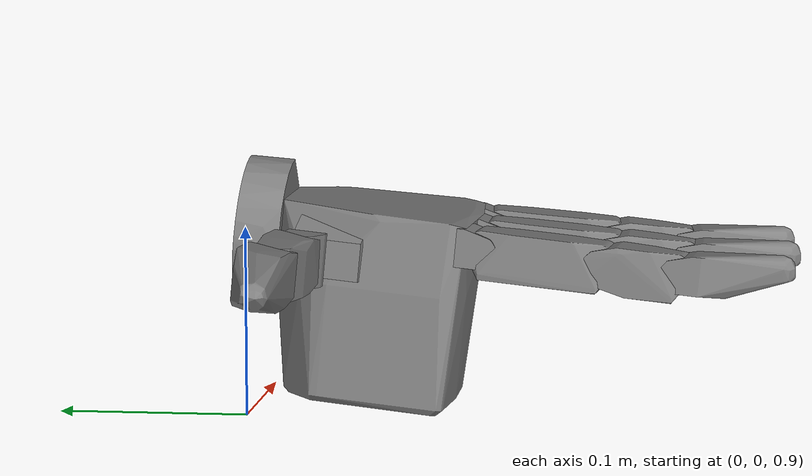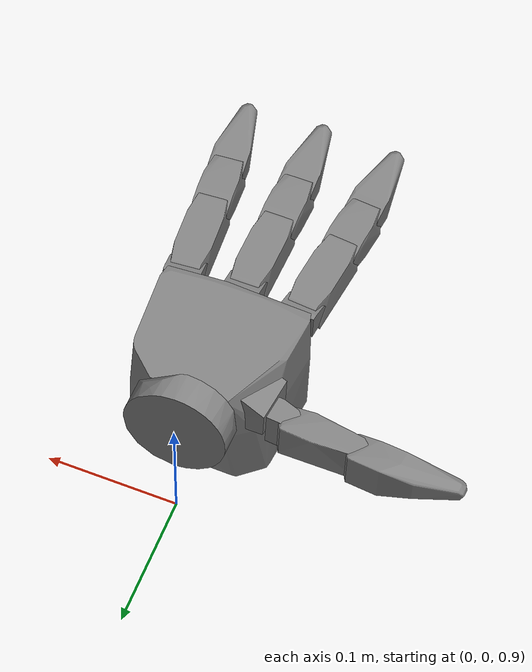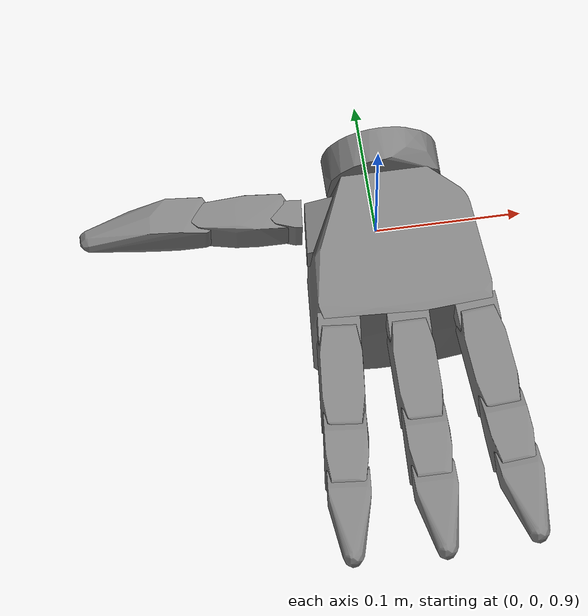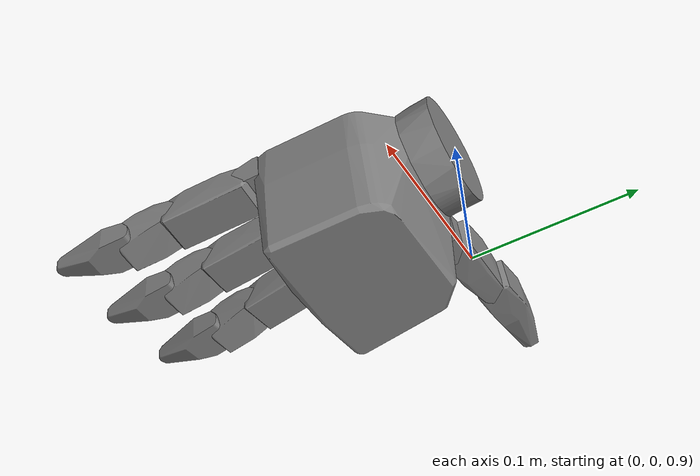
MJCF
<mujoco model="MuJoCo Model">
  <compiler angle="radian"/>

  <option timestep="0.01" impratio="10" cone="elliptic"/>

  <default>
    <geom friction="1 0.5 0.001"/>
  </default>

  <asset>
    <mesh name="mesh_17" vertex="0.038 0 0 0.036704 0.009837 0 0.037854 -0.003319 0 0.037423 -0.006597 0 0.035396 -0.013825 0 0.032909 0.019 0 0.031129 0.021795 0 0.031726 -0.020915 0 0.02987 -0.02349 0.003665 0.033776 -0.017413 0.003665 0.029108 0.024427 0 0.026871 0.026868 0 0.029108 -0.024427 0 0.026871 -0.026868 0 0.020737 -0.031843 0 0.01454 0.035108 0 0.01454 -0.035108 0 0.011622 -0.036179 0 0.00789 -0.037172 0 0 0.038 0 0 -0.038 0 -0.006864 -0.037375 0 -0.01454 0.035108 0 -0.01454 -0.035108 0 -0.021441 -0.031373 0 -0.026871 0.026868 0 -0.027003 -0.026736 0 -0.024885 -0.028718 0.003665 -0.031129 0.021795 0 -0.032909 -0.019 0 -0.035709 0.012995 0 -0.037423 0.006597 0 -0.038 0 0 -0.035709 -0.012995 0 0.037854 -0.003319 0.023 0.037854 0.003319 0.023 0.036704 0.009837 0.023 0.035278 0.014123 0.022008 0.032909 0.019 0.023 0.031129 0.021795 0.023 0.029108 0.024427 0.023 0.031129 -0.021795 0.023 0.026871 0.026868 0.023 0.023134 0.030146 0.023 0.017064 0.033953 0.023 0.013381 -0.035566 0.023 0.002379 -0.037925 0.023 0 0.038 0.023 -0.008678 -0.036996 0.023 -0.019 -0.032909 0.023 -0.019682 0.032505 0.023 -0.026871 -0.026868 0.023 -0.029108 0.024427 0.023 -0.02987 -0.02349 0.022008 -0.034439 0.016061 0.023 -0.037828 0.003612 0.014671 0.037828 -0.003612 0.01834 -0.037313 -0.007192 0.007334 0.027502 -0.026223 0.007334 0.035278 -0.014123 0.007334 -0.035278 -0.014123 0.014671 0.022042 -0.030954 0.014671 0.036461 -0.010706 0.014671 -0.031968 -0.020544 0.01834" face="3 56 34 15 47 44 15 19 47 15 44 43 15 43 11 57 32 33 57 33 60 57 55 32 57 60 55 53 26 51 53 51 54 53 60 63 53 54 55 53 55 60 29 26 53 29 53 63 29 60 33 29 63 60 27 26 24 27 51 26 49 24 23 49 23 48 49 51 27 49 27 24 21 20 48 21 48 23 46 48 20 46 20 18 46 18 45 17 16 45 17 45 18 14 13 61 14 45 16 14 61 45 58 61 13 28 30 54 31 32 55 31 55 54 31 54 30 52 50 25 52 25 28 52 28 54 22 25 50 22 50 47 22 47 19 35 34 0 35 0 1 35 1 36 41 45 61 41 61 58 41 8 7 2 56 3 2 0 34 2 34 56 62 4 3 62 59 4 62 3 34 62 34 41 62 41 59 12 7 8 12 58 13 12 8 41 12 41 58 9 7 4 9 4 59 9 59 41 9 41 7 37 38 36 37 1 5 37 5 38 37 36 1 42 11 43 10 24 26 10 18 20 10 26 29 10 12 13 10 28 25 10 1 0 10 33 32 10 16 17 10 32 31 10 22 19 10 0 2 10 19 15 10 23 24 10 20 21 10 13 14 10 3 4 10 4 7 10 6 5 10 5 1 10 15 11 10 29 33 10 21 23 10 17 18 10 14 16 10 30 28 10 31 30 10 25 22 10 2 3 10 7 12 39 6 10 39 10 40 39 5 6 39 38 5 42 35 36 42 39 40 42 47 50 42 44 47 42 54 51 42 52 54 42 45 41 42 51 49 42 46 45 42 36 38 42 43 44 42 49 48 42 48 46 42 50 52 42 34 35 42 41 34 42 38 39 42 10 11 42 40 10"/>
    <mesh name="mesh_18" vertex="0.042337 0.018577 -0.0383 0.042337 0.003977 -0.0258 0.042337 0.019877 -0.0211 0.042337 0.019877 -0.0015 0.039246 -0.044791 -0.0015 0.040928 -0.025564 -0.0383 0.040928 0.043119 -0.0383 0.039106 0.063939 -0.0015 0.039106 0.063939 -0.0211 0.029566 -0.049867 -0.0408 -0.057863 -0.019223 -0.0408 -0.057863 0.036777 -0.0408 -0.028899 0.062306 -0.0378 -0.036892 0.060031 -0.0378 -0.043471 0.054953 -0.0408 -0.040424 0.057805 -0.0378 -0.043471 0.054953 -0.0378 0.029566 -0.049867 -0.0378 -0.036892 -0.042476 -0.0378 0.029566 0.067421 -0.0378 -0.028899 -0.044752 -0.0378 0.037137 -0.009223 0 -0.057863 0.036777 0 -0.057863 -0.019732 0 0.034248 0.0598 0 0.037137 0.026777 0 0.027748 0.065254 0 -0.028724 0.060313 0 -0.032706 0.059553 0 -0.036453 0.058004 0 -0.039811 0.055732 0 -0.042641 0.05283 0 -0.008738 -0.040047 0 0.031157 -0.046983 0 -0.004588 -0.044107 -0.003 -0.028637 0.059317 -0.0983 0.029566 0.067421 -0.0953 0.029828 0.064432 -0.0983 -0.044853 0.04684 -0.0983 -0.045897 0.051623 -0.0953 -0.043442 0.054986 -0.0953 -0.041197 0.052995 -0.0983 -0.040397 0.057825 -0.0953 -0.028899 0.062306 -0.0953 0.034769 0.065199 -0.0953 0.033078 0.061705 -0.0983 -0.045863 0.041069 -0.0983 0.039061 0.027734 -0.0953 -0.048863 -0.023514 -0.0953 0.039137 0.025991 -0.0953 -0.048563 -0.026961 -0.0953 -0.045608 -0.026444 -0.0983 0.029828 -0.046878 -0.0983 -0.028899 -0.044752 -0.0953 -0.036872 0.060041 -0.0953 0.036066 -0.044412 -0.0953 0.035411 -0.04666 -0.0953 0.03275 -0.045275 -0.0983 0.032975 -0.04915 -0.0953 -0.032173 -0.041112 -0.0983 0.039137 -0.008437 -0.0953 0.036137 -0.008437 -0.0983 -0.032993 -0.043998 -0.0953 -0.043442 -0.037431 -0.0408" face="12 26 19 27 26 12 43 37 35 43 36 37 39 46 11 4 3 21 34 32 23 34 23 18 63 23 10 63 18 23 63 10 50 63 62 18 63 50 62 1 4 5 1 3 4 25 21 3 7 26 24 7 19 26 7 24 25 7 25 3 7 3 6 7 6 8 44 36 8 44 45 37 44 37 36 44 8 6 53 59 52 53 62 59 58 52 57 58 57 56 58 56 4 58 9 53 58 53 52 58 17 9 58 4 17 47 44 6 47 45 44 2 6 3 0 60 49 0 49 47 0 47 6 0 5 60 0 1 5 0 6 2 55 60 5 55 5 4 55 4 56 55 56 57 61 49 60 61 55 57 61 60 55 61 45 47 61 47 49 15 13 42 15 16 30 15 30 29 15 29 13 28 13 29 28 12 13 28 27 12 54 43 35 54 35 41 54 41 42 54 42 13 54 12 43 54 13 12 48 10 11 48 50 10 48 11 46 51 59 62 51 62 50 51 48 46 51 50 48 38 46 39 38 39 41 40 42 41 40 41 39 40 15 42 40 11 14 40 39 11 40 14 16 40 16 15 31 16 22 31 30 16 33 4 21 33 32 34 33 17 4 33 34 17 20 17 34 20 34 18 20 18 62 20 62 53 22 11 10 22 10 23 43 12 19 43 19 36 7 36 19 7 8 36 0 3 1 0 2 3 14 22 16 14 11 22 38 52 59 38 35 37 38 41 35 38 45 61 38 37 45 38 57 52 38 59 51 38 61 57 38 51 46 33 25 24 33 31 22 33 23 32 33 29 30 33 24 26 33 22 23 33 26 27 33 28 29 33 21 25 33 27 28 33 30 31 20 53 9 20 9 17"/>
    <mesh name="mesh_19" vertex="0.003085 0.0135 0.004255 0.000796 0.0135 0.005378 -0.00166 0.0135 0.006068 -0.0042 0.0135 0.0063 0.0098 0.0135 -0.0114 0.0098 0.0135 -0.0157 -0.0098 0.0135 -0.0157 -0.0098 0.0135 0.0033 -0.009742 0.0135 0.003885 -0.0068 0.0135 0.0063 -0.007385 0.0135 0.006242 -0.009572 0.0135 0.004448 -0.007948 0.0135 0.006072 -0.009294 0.0135 0.004967 -0.008921 0.0135 0.005421 -0.008467 0.0135 0.005794 0.005133 0.0135 0.002735 0.005838 0.0135 0.001957 0.006364 0.0135 0.001049 0.00669 0.0135 5.2e-05 -0.0098 -0.0135 -0.0157 0.0098 -0.0135 -0.0157 0.0098 -0.0135 -0.0114 -0.0042 -0.0135 0.0063 -0.007385 -0.0135 0.006242 -0.007948 -0.0135 0.006072 0.003085 -0.0135 0.004255 0.000796 -0.0135 0.005378 -0.00166 -0.0135 0.006068 -0.0098 -0.0135 0.0033 -0.0068 -0.0135 0.0063 0.005133 -0.0135 0.002735 0.00669 -0.0135 5.2e-05 0.005838 -0.0135 0.001957 -0.009742 -0.0135 0.003885 -0.009572 -0.0135 0.004448 -0.008467 -0.0135 0.005794 -0.008921 -0.0135 0.005421 -0.009294 -0.0135 0.004967 0.006364 -0.0135 0.001049" face="7 6 20 7 20 29 5 21 20 5 20 6 5 22 21 5 4 22 34 8 7 34 7 29 11 34 35 11 8 34 28 1 2 28 27 1 0 27 26 0 1 27 32 22 4 32 4 19 32 19 18 32 18 39 23 2 3 23 28 2 23 3 9 23 9 30 33 18 17 33 39 18 16 31 33 16 33 17 16 0 26 16 26 31 14 8 11 14 7 8 14 9 3 14 19 4 14 4 5 14 3 2 14 17 18 14 6 7 14 5 6 14 11 13 14 15 12 14 12 10 14 2 1 14 1 0 14 16 17 14 10 9 14 18 19 14 0 16 25 12 15 25 15 36 37 15 14 37 36 15 24 9 10 24 30 9 24 10 12 24 12 25 38 13 11 38 11 35 38 37 14 38 14 13 38 21 22 38 23 30 38 20 21 38 29 20 38 35 34 38 26 27 38 34 29 38 36 37 38 27 28 38 22 32 38 31 26 38 39 33 38 32 39 38 28 23 38 33 31 38 25 36 38 30 24 38 24 25"/>
    <mesh name="mesh_20" vertex="-0.003 -0.0147 -0.01375 -0.003 -0.0147 0.01375 0.057 -0.0119 0.01425 0.057 -0.0147 0.01375 0.057 -0.0147 -0.01375 0.003645 -0.01045 0.01425 0.057 -0.0142 -0.01425 0.057 -0.014391 0.014212 -0.003 -0.0119 0.01425 0.0225 -0.0012 -0.01425 -0.003 -0.0119 -0.01425 0.057 -0.0119 -0.01425 0.0578 0.0098 -0.0108 0.062704 -0.005775 -0.0108 0.062419 -0.006713 -0.0108 0.061957 -0.007578 -0.0108 0.0628 -0.0048 -0.0108 0.0628 0.0048 -0.0108 0.061957 0.007578 -0.0108 0.062419 0.006713 -0.0108 0.058775 0.009704 -0.0108 0.059713 0.009419 -0.0108 0.060578 0.008957 -0.0108 0.041 0.0098 -0.0135 0.043778 0.008957 -0.0135 0.0628 0.0048 -0.0061 0.0628 -0.0048 -0.0061 0.058775 0.009704 0.0063 0.062704 0.005775 0.0063 0.061957 0.007578 0.0063 0.0578 0.0098 0.011 0.059713 0.009419 0.011 0.062704 -0.005775 0.011 0.041 0.0098 0.0135 0.043778 0.008957 0.0135 0.044536 0.008336 0.0135 0.041975 0.009704 0.0135 -0.0038 0.0098 0.011 -0.008419 -0.006713 0.011 -0.007957 -0.007578 0.011 -0.008704 -0.005775 0.011 -0.0088 -0.0048 0.011 -0.008419 0.006713 0.011 -0.006578 0.008957 0.011 -0.004775 0.009704 0.0063 -0.008704 0.005775 0.0063 0.013 0.0098 0.0135 0.011087 0.009419 0.0135 -0.0088 0.0048 -0.0061 -0.008419 0.006713 -0.0061 0.011087 0.009419 -0.0135 0.009464 0.008336 -0.0135 0.013 0.0098 -0.0135 -0.0038 0.0098 -0.0108 -0.004775 0.009704 -0.0108 -0.005713 0.009419 -0.0108 -0.008704 0.005775 -0.0108 -0.007957 0.007578 -0.0108 -0.006578 0.008957 -0.0108 -0.0088 0.0048 -0.0108 -0.0088 -0.0048 -0.0108 -0.007957 -0.007578 -0.0108 -0.008419 -0.006713 -0.0108 -0.008704 -0.005775 -0.0108" face="3 7 1 3 4 15 17 28 25 55 44 54 55 50 58 55 54 50 29 31 28 29 22 31 29 18 22 32 7 3 32 26 25 32 25 28 32 28 31 32 3 15 32 31 2 32 2 7 10 56 57 10 50 9 10 59 56 10 60 59 10 63 60 10 0 63 51 58 50 51 57 58 51 50 10 51 10 57 38 39 1 38 1 40 62 0 61 62 63 0 35 31 34 35 2 31 35 34 2 36 34 31 36 30 33 36 31 30 36 33 2 36 2 34 27 30 31 12 20 23 46 37 47 5 46 47 5 33 46 5 2 33 21 31 22 24 22 18 24 21 22 24 18 11 24 11 9 24 9 23 24 20 21 24 23 20 19 28 17 19 18 29 19 29 28 19 11 18 19 17 11 43 37 44 43 47 37 43 55 58 43 44 55 43 58 57 43 57 42 8 42 41 8 41 40 8 40 1 8 5 47 8 47 43 8 43 42 8 1 7 8 7 2 8 2 5 45 48 41 45 41 42 49 57 56 49 42 57 52 9 50 52 23 9 52 54 53 52 50 54 14 15 4 14 13 32 14 32 15 6 16 13 6 4 0 6 0 10 6 14 4 6 13 14 61 1 39 61 0 1 54 37 53 54 44 37 3 1 0 3 0 4 17 25 26 17 26 16 32 16 26 32 13 16 60 63 40 60 40 41 60 41 48 60 48 59 62 61 39 62 39 38 62 40 63 62 38 40 12 27 20 12 30 27 21 20 27 21 27 31 45 59 48 45 56 59 49 56 45 49 45 42 52 53 37 52 37 46 52 12 23 52 33 30 52 30 12 52 46 33 6 17 16 6 11 17 6 9 11 6 10 9"/>
    <mesh name="mesh_21" vertex="0.043175 -0.009704 -0.0061 0.0472 -0.0048 -0.0061 0.0422 -0.0098 -0.0061 0.044113 -0.009419 -0.0061 0.047104 -0.005775 -0.0061 0.046819 -0.006713 -0.0061 0.046357 -0.007578 -0.0061 0.045736 -0.008336 -0.0061 0.044978 -0.008957 -0.0061 0.0422 0.0098 0.0063 0.044113 0.009419 -0.0061 -0.004255 0.003085 -0.0135 -0.005378 0.000796 -0.0115 -0.006068 -0.00166 -0.0135 -0.006068 -0.00166 -0.0115 -0.0063 -0.0042 -0.0135 -0.0063 -0.0042 -0.0115 0.0114 0.0098 -0.0135 -0.0033 -0.0098 -0.0135 -0.0063 -0.0068 -0.0135 -0.004448 -0.009572 -0.0135 -0.006072 -0.007948 -0.0135 -0.006242 -0.007385 -0.0135 -0.005794 -0.008467 -0.0135 -5.2e-05 0.00669 -0.0135 0.0157 -0.0098 -0.0111 -0.004448 -0.009572 -0.0115 -0.005794 -0.008467 -0.0115 -0.004255 0.003085 0.0135 -0.005378 0.000796 0.0135 -0.003885 -0.009742 0.0135 -0.004967 -0.009294 0.0135 0.0114 0.0098 0.0135 -5.2e-05 0.00669 0.0113 -0.001049 0.006364 0.0135 -0.001957 0.005838 0.0113 -0.002735 0.005133 0.0113 -0.006242 -0.007385 0.0113 -0.0063 -0.0068 0.0113 0.0422 0.0098 0.011 0.043175 0.009704 0.011 0.044113 0.009419 0.011 0.047104 0.005775 0.011 0.0472 0.0048 0.011 0.0472 -0.0048 0.011 0.046357 -0.007578 0.011 0.047104 -0.005775 0.011 0.045736 0.008336 0.011 0.028178 0.008957 0.0135 0.028936 0.008336 0.0135 0.026375 0.009704 0.0135 0.0254 0.0098 -0.0108 0.0472 0.0048 -0.0108 0.045736 0.008336 -0.0108 0.027313 0.009419 -0.0135 0.0414 -0.0119 0.01425 0.0414 -0.0142 0.01425 0.0414 -0.0147 0.01375 0.0113 0.0055 0.01425 0.015261 0.006561 0.01425 0.014774 0.006886 0.01425 0.0128 0.007 0.01425 0.0157 0.0055 -0.01425 0.0176 -0.0147 0.01375" face="25 57 18 13 62 15 8 7 57 2 0 57 2 57 25 2 25 0 63 18 57 40 9 39 40 50 41 40 39 50 3 57 0 3 8 57 3 0 25 6 57 7 6 45 57 19 15 62 19 62 22 21 62 23 21 22 62 21 23 27 21 37 22 21 27 37 20 62 18 20 23 62 20 18 63 20 63 30 20 30 26 31 26 30 31 37 27 31 27 23 31 20 26 31 23 20 31 58 29 31 30 63 38 14 16 38 29 14 38 31 29 38 37 31 11 13 12 11 62 13 11 24 62 17 54 62 17 62 24 17 51 54 28 34 36 28 29 58 28 58 34 61 34 58 61 60 50 33 24 34 35 36 34 35 34 24 35 11 36 35 24 11 56 63 57 56 45 46 56 57 45 56 46 44 56 31 63 56 58 31 43 42 55 47 49 55 47 55 42 47 42 53 48 41 50 48 47 41 48 49 47 48 50 60 48 60 59 48 59 55 48 55 49 32 50 39 32 33 34 32 34 61 32 61 50 52 1 4 52 53 42 52 42 43 52 6 7 52 7 8 52 3 25 52 8 3 52 54 53 52 62 54 52 18 62 52 25 18 10 9 40 10 51 9 10 54 51 10 53 54 5 4 46 5 45 6 5 46 45 5 52 4 5 6 52 13 14 29 13 29 12 16 14 13 16 13 15 46 4 1 46 1 44 38 16 15 38 15 19 38 22 37 38 19 22 28 12 29 28 11 12 28 36 11 56 59 60 56 60 61 56 61 58 56 55 59 43 55 56 43 56 44 32 51 17 32 9 51 32 39 9 32 17 24 32 24 33 52 44 1 52 43 44 10 41 47 10 47 53 10 40 41"/>
    <mesh name="mesh_22" vertex="-0.001049 0.006364 -0.0135 -0.002735 0.005133 -0.0115 -0.005378 0.000796 -0.0135 -0.004255 0.003085 -0.0115 -0.006068 -0.00166 -0.0135 -0.006068 -0.00166 -0.0115 -0.0063 -0.0042 -0.0135 0.0157 0.0098 -0.0135 0.0157 -0.0098 -0.0135 -0.0033 -0.0098 -0.0135 -0.004448 -0.009572 -0.0135 -0.005794 -0.008467 -0.0135 -0.006242 -0.007385 -0.0115 0.028901 -0.0098 0.007378 0.028901 -0.0098 -0.007481 0.028901 -0.009094 0.008698 0.028901 -0.009335 0.008501 0.028901 -0.009679 0.007986 0.028901 -0.009769 0.007688 0.0114 0.009809 -0.0111 0.061458 0.004299 0.001597 0.057234 0.001073 -0.003798 0.057966 0.001339 0.003613 0.060583 0.002291 0.001107 0.057193 0.001186 -0.004405 0.056899 0.001993 0.005162 0.056984 0.00176 0.005032 0.059598 0.002061 0.003471 0.061262 0.002667 -0.000506 0.058027 0.001856 -0.004814 0.060475 0.002747 -0.003309 0.058027 0.001856 0.004711 0.058892 0.002719 0.004711 0.061771 0.003767 0.000494 0.05623 0.008039 0.006719 0.058897 0.008285 -0.005597 0.05623 0.008039 -0.006821 0.061282 0.008431 -0.002105 0.061282 0.008431 0.002003 0.059014 0.007606 0.005326 0.055283 0.006434 0.006663 0.054504 0.012688 0.004443 0.054225 0.013455 0.003303 0.054032 0.013985 0.00202 0.054033 0.013984 -0.002127 0.054226 0.013453 -0.00341 0.056987 0.009705 0.006154 0.056179 0.011927 -0.005169 0.060344 0.011101 -0.002302 0.055307 0.01432 0.000598 0.058819 0.013145 0.00032 0.056931 0.013442 0.002748 0.058987 0.012685 0.00191 0.056174 0.01194 0.005056 0.05527 0.010584 0.006106 0.056561 0.010877 0.005728 0.0157 -0.0098 0.0134 -0.0033 -0.0098 0.0134 0.0157 0.0098 0.0134 0.0114 0.0098 0.0134 -0.001049 0.006364 0.0134 -0.005421 -0.008921 0.0134 -0.001957 0.005838 0.0112 -0.005378 0.000796 0.0134" face="58 56 34 13 18 56 23 13 14 21 23 14 22 18 13 22 13 23 8 36 29 8 7 36 8 29 14 12 6 11 12 61 6 12 11 61 10 61 11 10 57 61 10 9 57 37 33 30 28 33 23 28 30 33 28 23 21 28 21 30 35 29 36 35 30 29 35 37 30 35 48 37 50 52 48 46 34 39 46 58 34 46 54 58 46 39 52 55 53 58 55 58 54 55 54 46 55 52 53 55 46 52 43 58 42 41 58 53 41 42 58 51 50 49 51 52 50 51 49 43 51 43 42 51 53 52 51 41 53 51 42 41 3 62 1 3 1 2 63 60 62 63 6 61 63 5 6 63 62 3 4 6 5 44 45 7 44 19 49 44 7 19 44 49 50 44 50 45 47 36 7 47 7 45 47 35 36 47 48 35 47 50 48 47 45 50 59 19 60 59 49 19 59 43 49 59 58 43 0 60 19 0 62 60 0 1 62 0 19 7 0 2 1 24 14 29 24 21 14 24 29 30 24 30 21 40 34 56 40 56 25 26 56 31 26 25 56 26 31 25 15 31 56 15 56 16 15 16 31 17 31 16 17 18 22 17 22 31 17 56 18 17 16 56 27 22 23 27 31 22 27 23 33 27 33 20 32 39 34 32 25 31 32 31 27 32 34 40 32 40 25 32 20 39 32 27 20 38 52 39 38 39 20 38 48 52 38 37 48 38 20 33 38 33 37 8 13 56 8 56 57 8 14 13 8 57 9 63 3 2 4 5 63 4 63 2 59 57 56 59 56 58 59 60 63 59 61 57 59 63 61 0 9 10 0 11 6 0 8 9 0 6 4 0 7 8 0 10 11 0 4 2"/>
    <mesh name="mesh_23" vertex="0.003085 0.0135 0.004255 0.000796 0.0135 0.005378 -0.00166 0.0135 0.006068 -0.0042 0.0135 0.0063 0.0098 0.0135 -0.0114 0.0098 0.0135 -0.0157 -0.0098 0.0135 -0.0157 -0.0098 0.0135 0.0033 -0.009742 0.0135 0.003885 -0.0068 0.0135 0.0063 -0.007385 0.0135 0.006242 -0.009572 0.0135 0.004448 -0.007948 0.0135 0.006072 -0.009294 0.0135 0.004967 -0.008921 0.0135 0.005421 -0.008467 0.0135 0.005794 0.005133 0.0135 0.002735 0.005838 0.0135 0.001957 0.006364 0.0135 0.001049 0.00669 0.0135 5.2e-05 -0.0098 -0.0135 -0.0157 0.0098 -0.0135 -0.0157 0.0098 -0.0135 -0.0114 -0.0042 -0.0135 0.0063 -0.007385 -0.0135 0.006242 -0.007948 -0.0135 0.006072 0.003085 -0.0135 0.004255 0.000796 -0.0135 0.005378 -0.00166 -0.0135 0.006068 -0.0098 -0.0135 0.0033 -0.0068 -0.0135 0.0063 0.005133 -0.0135 0.002735 0.00669 -0.0135 5.2e-05 0.005838 -0.0135 0.001957 -0.009742 -0.0135 0.003885 -0.009572 -0.0135 0.004448 -0.008467 -0.0135 0.005794 -0.008921 -0.0135 0.005421 -0.009294 -0.0135 0.004967 0.006364 -0.0135 0.001049" face="7 6 20 7 20 29 5 21 20 5 20 6 5 22 21 5 4 22 34 8 7 34 7 29 11 34 35 11 8 34 28 1 2 28 27 1 0 27 26 0 1 27 32 22 4 32 4 19 32 19 18 32 18 39 23 2 3 23 28 2 23 3 9 23 9 30 33 18 17 33 39 18 16 31 33 16 33 17 16 0 26 16 26 31 14 8 11 14 7 8 14 9 3 14 19 4 14 4 5 14 3 2 14 17 18 14 6 7 14 5 6 14 11 13 14 15 12 14 12 10 14 2 1 14 1 0 14 16 17 14 10 9 14 18 19 14 0 16 25 12 15 25 15 36 37 15 14 37 36 15 24 9 10 24 30 9 24 10 12 24 12 25 38 13 11 38 11 35 38 37 14 38 14 13 38 21 22 38 23 30 38 20 21 38 29 20 38 35 34 38 26 27 38 34 29 38 36 37 38 27 28 38 22 32 38 31 26 38 39 33 38 32 39 38 28 23 38 33 31 38 25 36 38 30 24 38 24 25"/>
    <mesh name="mesh_24" vertex="-0.003 -0.0147 -0.01375 -0.003 -0.0147 0.01375 0.057 -0.0119 0.01425 0.057 -0.0147 0.01375 0.057 -0.0147 -0.01375 0.003645 -0.01045 0.01425 0.057 -0.0142 -0.01425 0.057 -0.014391 0.014212 -0.003 -0.0119 0.01425 0.0225 -0.0012 -0.01425 -0.003 -0.0119 -0.01425 0.057 -0.0119 -0.01425 0.0578 0.0098 -0.0108 0.062704 -0.005775 -0.0108 0.062419 -0.006713 -0.0108 0.061957 -0.007578 -0.0108 0.0628 -0.0048 -0.0108 0.0628 0.0048 -0.0108 0.061957 0.007578 -0.0108 0.062419 0.006713 -0.0108 0.058775 0.009704 -0.0108 0.059713 0.009419 -0.0108 0.060578 0.008957 -0.0108 0.041 0.0098 -0.0135 0.043778 0.008957 -0.0135 0.0628 0.0048 -0.0061 0.0628 -0.0048 -0.0061 0.058775 0.009704 0.0063 0.062704 0.005775 0.0063 0.061957 0.007578 0.0063 0.0578 0.0098 0.011 0.059713 0.009419 0.011 0.062704 -0.005775 0.011 0.041 0.0098 0.0135 0.043778 0.008957 0.0135 0.044536 0.008336 0.0135 0.041975 0.009704 0.0135 -0.0038 0.0098 0.011 -0.008419 -0.006713 0.011 -0.007957 -0.007578 0.011 -0.008704 -0.005775 0.011 -0.0088 -0.0048 0.011 -0.008419 0.006713 0.011 -0.006578 0.008957 0.011 -0.004775 0.009704 0.0063 -0.008704 0.005775 0.0063 0.013 0.0098 0.0135 0.011087 0.009419 0.0135 -0.0088 0.0048 -0.0061 -0.008419 0.006713 -0.0061 0.011087 0.009419 -0.0135 0.009464 0.008336 -0.0135 0.013 0.0098 -0.0135 -0.0038 0.0098 -0.0108 -0.004775 0.009704 -0.0108 -0.005713 0.009419 -0.0108 -0.008704 0.005775 -0.0108 -0.007957 0.007578 -0.0108 -0.006578 0.008957 -0.0108 -0.0088 0.0048 -0.0108 -0.0088 -0.0048 -0.0108 -0.007957 -0.007578 -0.0108 -0.008419 -0.006713 -0.0108 -0.008704 -0.005775 -0.0108" face="3 7 1 3 4 15 17 28 25 55 44 54 55 50 58 55 54 50 29 31 28 29 22 31 29 18 22 32 7 3 32 26 25 32 25 28 32 28 31 32 3 15 32 31 2 32 2 7 10 56 57 10 50 9 10 59 56 10 60 59 10 63 60 10 0 63 51 58 50 51 57 58 51 50 10 51 10 57 38 39 1 38 1 40 62 0 61 62 63 0 35 31 34 35 2 31 35 34 2 36 34 31 36 30 33 36 31 30 36 33 2 36 2 34 27 30 31 12 20 23 46 37 47 5 46 47 5 33 46 5 2 33 21 31 22 24 22 18 24 21 22 24 18 11 24 11 9 24 9 23 24 20 21 24 23 20 19 28 17 19 18 29 19 29 28 19 11 18 19 17 11 43 37 44 43 47 37 43 55 58 43 44 55 43 58 57 43 57 42 8 42 41 8 41 40 8 40 1 8 5 47 8 47 43 8 43 42 8 1 7 8 7 2 8 2 5 45 48 41 45 41 42 49 57 56 49 42 57 52 9 50 52 23 9 52 54 53 52 50 54 14 15 4 14 13 32 14 32 15 6 16 13 6 4 0 6 0 10 6 14 4 6 13 14 61 1 39 61 0 1 54 37 53 54 44 37 3 1 0 3 0 4 17 25 26 17 26 16 32 16 26 32 13 16 60 63 40 60 40 41 60 41 48 60 48 59 62 61 39 62 39 38 62 40 63 62 38 40 12 27 20 12 30 27 21 20 27 21 27 31 45 59 48 45 56 59 49 56 45 49 45 42 52 53 37 52 37 46 52 12 23 52 33 30 52 30 12 52 46 33 6 17 16 6 11 17 6 9 11 6 10 9"/>
    <mesh name="mesh_25" vertex="0.043175 -0.009704 -0.0061 0.0472 -0.0048 -0.0061 0.0422 -0.0098 -0.0061 0.044113 -0.009419 -0.0061 0.047104 -0.005775 -0.0061 0.046819 -0.006713 -0.0061 0.046357 -0.007578 -0.0061 0.045736 -0.008336 -0.0061 0.044978 -0.008957 -0.0061 0.0422 0.0098 0.0063 0.044113 0.009419 -0.0061 -0.004255 0.003085 -0.0135 -0.005378 0.000796 -0.0115 -0.006068 -0.00166 -0.0135 -0.006068 -0.00166 -0.0115 -0.0063 -0.0042 -0.0135 -0.0063 -0.0042 -0.0115 0.0114 0.0098 -0.0135 -0.0033 -0.0098 -0.0135 -0.0063 -0.0068 -0.0135 -0.004448 -0.009572 -0.0135 -0.006072 -0.007948 -0.0135 -0.006242 -0.007385 -0.0135 -0.005794 -0.008467 -0.0135 -5.2e-05 0.00669 -0.0135 0.0157 -0.0098 -0.0111 -0.004448 -0.009572 -0.0115 -0.005794 -0.008467 -0.0115 -0.004255 0.003085 0.0135 -0.005378 0.000796 0.0135 -0.003885 -0.009742 0.0135 -0.004967 -0.009294 0.0135 0.0114 0.0098 0.0135 -5.2e-05 0.00669 0.0113 -0.001049 0.006364 0.0135 -0.001957 0.005838 0.0113 -0.002735 0.005133 0.0113 -0.006242 -0.007385 0.0113 -0.0063 -0.0068 0.0113 0.0422 0.0098 0.011 0.043175 0.009704 0.011 0.044113 0.009419 0.011 0.047104 0.005775 0.011 0.0472 0.0048 0.011 0.0472 -0.0048 0.011 0.046357 -0.007578 0.011 0.047104 -0.005775 0.011 0.045736 0.008336 0.011 0.028178 0.008957 0.0135 0.028936 0.008336 0.0135 0.026375 0.009704 0.0135 0.0254 0.0098 -0.0108 0.0472 0.0048 -0.0108 0.045736 0.008336 -0.0108 0.027313 0.009419 -0.0135 0.0414 -0.0119 0.01425 0.0414 -0.0142 0.01425 0.0414 -0.0147 0.01375 0.0113 0.0055 0.01425 0.015261 0.006561 0.01425 0.014774 0.006886 0.01425 0.0128 0.007 0.01425 0.0157 0.0055 -0.01425 0.0176 -0.0147 0.01375" face="25 57 18 13 62 15 8 7 57 2 0 57 2 57 25 2 25 0 63 18 57 40 9 39 40 50 41 40 39 50 3 57 0 3 8 57 3 0 25 6 57 7 6 45 57 19 15 62 19 62 22 21 62 23 21 22 62 21 23 27 21 37 22 21 27 37 20 62 18 20 23 62 20 18 63 20 63 30 20 30 26 31 26 30 31 37 27 31 27 23 31 20 26 31 23 20 31 58 29 31 30 63 38 14 16 38 29 14 38 31 29 38 37 31 11 13 12 11 62 13 11 24 62 17 54 62 17 62 24 17 51 54 28 34 36 28 29 58 28 58 34 61 34 58 61 60 50 33 24 34 35 36 34 35 34 24 35 11 36 35 24 11 56 63 57 56 45 46 56 57 45 56 46 44 56 31 63 56 58 31 43 42 55 47 49 55 47 55 42 47 42 53 48 41 50 48 47 41 48 49 47 48 50 60 48 60 59 48 59 55 48 55 49 32 50 39 32 33 34 32 34 61 32 61 50 52 1 4 52 53 42 52 42 43 52 6 7 52 7 8 52 3 25 52 8 3 52 54 53 52 62 54 52 18 62 52 25 18 10 9 40 10 51 9 10 54 51 10 53 54 5 4 46 5 45 6 5 46 45 5 52 4 5 6 52 13 14 29 13 29 12 16 14 13 16 13 15 46 4 1 46 1 44 38 16 15 38 15 19 38 22 37 38 19 22 28 12 29 28 11 12 28 36 11 56 59 60 56 60 61 56 61 58 56 55 59 43 55 56 43 56 44 32 51 17 32 9 51 32 39 9 32 17 24 32 24 33 52 44 1 52 43 44 10 41 47 10 47 53 10 40 41"/>
    <mesh name="mesh_26" vertex="-0.001049 0.006364 -0.0135 -0.002735 0.005133 -0.0115 -0.005378 0.000796 -0.0135 -0.004255 0.003085 -0.0115 -0.006068 -0.00166 -0.0135 -0.006068 -0.00166 -0.0115 -0.0063 -0.0042 -0.0135 0.0157 0.0098 -0.0135 0.0157 -0.0098 -0.0135 -0.0033 -0.0098 -0.0135 -0.004448 -0.009572 -0.0135 -0.005794 -0.008467 -0.0135 -0.006242 -0.007385 -0.0115 0.028901 -0.0098 0.007378 0.028901 -0.0098 -0.007481 0.028901 -0.009094 0.008698 0.028901 -0.009335 0.008501 0.028901 -0.009679 0.007986 0.028901 -0.009769 0.007688 0.0114 0.009809 -0.0111 0.061458 0.004299 0.001597 0.057234 0.001073 -0.003798 0.057966 0.001339 0.003613 0.060583 0.002291 0.001107 0.057193 0.001186 -0.004405 0.056899 0.001993 0.005162 0.056984 0.00176 0.005032 0.059598 0.002061 0.003471 0.061262 0.002667 -0.000506 0.058027 0.001856 -0.004814 0.060475 0.002747 -0.003309 0.058027 0.001856 0.004711 0.058892 0.002719 0.004711 0.061771 0.003767 0.000494 0.05623 0.008039 0.006719 0.058897 0.008285 -0.005597 0.05623 0.008039 -0.006821 0.061282 0.008431 -0.002105 0.061282 0.008431 0.002003 0.059014 0.007606 0.005326 0.055283 0.006434 0.006663 0.054504 0.012688 0.004443 0.054225 0.013455 0.003303 0.054032 0.013985 0.00202 0.054033 0.013984 -0.002127 0.054226 0.013453 -0.00341 0.056987 0.009705 0.006154 0.056179 0.011927 -0.005169 0.060344 0.011101 -0.002302 0.055307 0.01432 0.000598 0.058819 0.013145 0.00032 0.056931 0.013442 0.002748 0.058987 0.012685 0.00191 0.056174 0.01194 0.005056 0.05527 0.010584 0.006106 0.056561 0.010877 0.005728 0.0157 -0.0098 0.0134 -0.0033 -0.0098 0.0134 0.0157 0.0098 0.0134 0.0114 0.0098 0.0134 -0.001049 0.006364 0.0134 -0.005421 -0.008921 0.0134 -0.001957 0.005838 0.0112 -0.005378 0.000796 0.0134" face="58 56 34 13 18 56 23 13 14 21 23 14 22 18 13 22 13 23 8 36 29 8 7 36 8 29 14 12 6 11 12 61 6 12 11 61 10 61 11 10 57 61 10 9 57 37 33 30 28 33 23 28 30 33 28 23 21 28 21 30 35 29 36 35 30 29 35 37 30 35 48 37 50 52 48 46 34 39 46 58 34 46 54 58 46 39 52 55 53 58 55 58 54 55 54 46 55 52 53 55 46 52 43 58 42 41 58 53 41 42 58 51 50 49 51 52 50 51 49 43 51 43 42 51 53 52 51 41 53 51 42 41 3 62 1 3 1 2 63 60 62 63 6 61 63 5 6 63 62 3 4 6 5 44 45 7 44 19 49 44 7 19 44 49 50 44 50 45 47 36 7 47 7 45 47 35 36 47 48 35 47 50 48 47 45 50 59 19 60 59 49 19 59 43 49 59 58 43 0 60 19 0 62 60 0 1 62 0 19 7 0 2 1 24 14 29 24 21 14 24 29 30 24 30 21 40 34 56 40 56 25 26 56 31 26 25 56 26 31 25 15 31 56 15 56 16 15 16 31 17 31 16 17 18 22 17 22 31 17 56 18 17 16 56 27 22 23 27 31 22 27 23 33 27 33 20 32 39 34 32 25 31 32 31 27 32 34 40 32 40 25 32 20 39 32 27 20 38 52 39 38 39 20 38 48 52 38 37 48 38 20 33 38 33 37 8 13 56 8 56 57 8 14 13 8 57 9 63 3 2 4 5 63 4 63 2 59 57 56 59 56 58 59 60 63 59 61 57 59 63 61 0 9 10 0 11 6 0 8 9 0 6 4 0 7 8 0 10 11 0 4 2"/>
    <mesh name="mesh_27" vertex="0.003085 0.0135 0.004255 0.000796 0.0135 0.005378 -0.00166 0.0135 0.006068 -0.0042 0.0135 0.0063 0.0098 0.0135 -0.0114 0.0098 0.0135 -0.0157 -0.0098 0.0135 -0.0157 -0.0098 0.0135 0.0033 -0.009742 0.0135 0.003885 -0.0068 0.0135 0.0063 -0.007385 0.0135 0.006242 -0.009572 0.0135 0.004448 -0.007948 0.0135 0.006072 -0.009294 0.0135 0.004967 -0.008921 0.0135 0.005421 -0.008467 0.0135 0.005794 0.005133 0.0135 0.002735 0.005838 0.0135 0.001957 0.006364 0.0135 0.001049 0.00669 0.0135 5.2e-05 -0.0098 -0.0135 -0.0157 0.0098 -0.0135 -0.0157 0.0098 -0.0135 -0.0114 -0.0042 -0.0135 0.0063 -0.007385 -0.0135 0.006242 -0.007948 -0.0135 0.006072 0.003085 -0.0135 0.004255 0.000796 -0.0135 0.005378 -0.00166 -0.0135 0.006068 -0.0098 -0.0135 0.0033 -0.0068 -0.0135 0.0063 0.005133 -0.0135 0.002735 0.00669 -0.0135 5.2e-05 0.005838 -0.0135 0.001957 -0.009742 -0.0135 0.003885 -0.009572 -0.0135 0.004448 -0.008467 -0.0135 0.005794 -0.008921 -0.0135 0.005421 -0.009294 -0.0135 0.004967 0.006364 -0.0135 0.001049" face="7 6 20 7 20 29 5 21 20 5 20 6 5 22 21 5 4 22 34 8 7 34 7 29 11 34 35 11 8 34 28 1 2 28 27 1 0 27 26 0 1 27 32 22 4 32 4 19 32 19 18 32 18 39 23 2 3 23 28 2 23 3 9 23 9 30 33 18 17 33 39 18 16 31 33 16 33 17 16 0 26 16 26 31 14 8 11 14 7 8 14 9 3 14 19 4 14 4 5 14 3 2 14 17 18 14 6 7 14 5 6 14 11 13 14 15 12 14 12 10 14 2 1 14 1 0 14 16 17 14 10 9 14 18 19 14 0 16 25 12 15 25 15 36 37 15 14 37 36 15 24 9 10 24 30 9 24 10 12 24 12 25 38 13 11 38 11 35 38 37 14 38 14 13 38 21 22 38 23 30 38 20 21 38 29 20 38 35 34 38 26 27 38 34 29 38 36 37 38 27 28 38 22 32 38 31 26 38 39 33 38 32 39 38 28 23 38 33 31 38 25 36 38 30 24 38 24 25"/>
    <mesh name="mesh_28" vertex="-0.003 -0.0147 -0.01375 -0.003 -0.0147 0.01375 0.057 -0.0119 0.01425 0.057 -0.0147 0.01375 0.057 -0.0147 -0.01375 0.003645 -0.01045 0.01425 0.057 -0.0142 -0.01425 0.057 -0.014391 0.014212 -0.003 -0.0119 0.01425 0.0225 -0.0012 -0.01425 -0.003 -0.0119 -0.01425 0.057 -0.0119 -0.01425 0.0578 0.0098 -0.0108 0.062704 -0.005775 -0.0108 0.062419 -0.006713 -0.0108 0.061957 -0.007578 -0.0108 0.0628 -0.0048 -0.0108 0.0628 0.0048 -0.0108 0.061957 0.007578 -0.0108 0.062419 0.006713 -0.0108 0.058775 0.009704 -0.0108 0.059713 0.009419 -0.0108 0.060578 0.008957 -0.0108 0.041 0.0098 -0.0135 0.043778 0.008957 -0.0135 0.0628 0.0048 -0.0061 0.0628 -0.0048 -0.0061 0.058775 0.009704 0.0063 0.062704 0.005775 0.0063 0.061957 0.007578 0.0063 0.0578 0.0098 0.011 0.059713 0.009419 0.011 0.062704 -0.005775 0.011 0.041 0.0098 0.0135 0.043778 0.008957 0.0135 0.044536 0.008336 0.0135 0.041975 0.009704 0.0135 -0.0038 0.0098 0.011 -0.008419 -0.006713 0.011 -0.007957 -0.007578 0.011 -0.008704 -0.005775 0.011 -0.0088 -0.0048 0.011 -0.008419 0.006713 0.011 -0.006578 0.008957 0.011 -0.004775 0.009704 0.0063 -0.008704 0.005775 0.0063 0.013 0.0098 0.0135 0.011087 0.009419 0.0135 -0.0088 0.0048 -0.0061 -0.008419 0.006713 -0.0061 0.011087 0.009419 -0.0135 0.009464 0.008336 -0.0135 0.013 0.0098 -0.0135 -0.0038 0.0098 -0.0108 -0.004775 0.009704 -0.0108 -0.005713 0.009419 -0.0108 -0.008704 0.005775 -0.0108 -0.007957 0.007578 -0.0108 -0.006578 0.008957 -0.0108 -0.0088 0.0048 -0.0108 -0.0088 -0.0048 -0.0108 -0.007957 -0.007578 -0.0108 -0.008419 -0.006713 -0.0108 -0.008704 -0.005775 -0.0108" face="3 7 1 3 4 15 17 28 25 55 44 54 55 50 58 55 54 50 29 31 28 29 22 31 29 18 22 32 7 3 32 26 25 32 25 28 32 28 31 32 3 15 32 31 2 32 2 7 10 56 57 10 50 9 10 59 56 10 60 59 10 63 60 10 0 63 51 58 50 51 57 58 51 50 10 51 10 57 38 39 1 38 1 40 62 0 61 62 63 0 35 31 34 35 2 31 35 34 2 36 34 31 36 30 33 36 31 30 36 33 2 36 2 34 27 30 31 12 20 23 46 37 47 5 46 47 5 33 46 5 2 33 21 31 22 24 22 18 24 21 22 24 18 11 24 11 9 24 9 23 24 20 21 24 23 20 19 28 17 19 18 29 19 29 28 19 11 18 19 17 11 43 37 44 43 47 37 43 55 58 43 44 55 43 58 57 43 57 42 8 42 41 8 41 40 8 40 1 8 5 47 8 47 43 8 43 42 8 1 7 8 7 2 8 2 5 45 48 41 45 41 42 49 57 56 49 42 57 52 9 50 52 23 9 52 54 53 52 50 54 14 15 4 14 13 32 14 32 15 6 16 13 6 4 0 6 0 10 6 14 4 6 13 14 61 1 39 61 0 1 54 37 53 54 44 37 3 1 0 3 0 4 17 25 26 17 26 16 32 16 26 32 13 16 60 63 40 60 40 41 60 41 48 60 48 59 62 61 39 62 39 38 62 40 63 62 38 40 12 27 20 12 30 27 21 20 27 21 27 31 45 59 48 45 56 59 49 56 45 49 45 42 52 53 37 52 37 46 52 12 23 52 33 30 52 30 12 52 46 33 6 17 16 6 11 17 6 9 11 6 10 9"/>
    <mesh name="mesh_29" vertex="0.043175 -0.009704 -0.0061 0.0472 -0.0048 -0.0061 0.0422 -0.0098 -0.0061 0.044113 -0.009419 -0.0061 0.047104 -0.005775 -0.0061 0.046819 -0.006713 -0.0061 0.046357 -0.007578 -0.0061 0.045736 -0.008336 -0.0061 0.044978 -0.008957 -0.0061 0.0422 0.0098 0.0063 0.044113 0.009419 -0.0061 -0.004255 0.003085 -0.0135 -0.005378 0.000796 -0.0115 -0.006068 -0.00166 -0.0135 -0.006068 -0.00166 -0.0115 -0.0063 -0.0042 -0.0135 -0.0063 -0.0042 -0.0115 0.0114 0.0098 -0.0135 -0.0033 -0.0098 -0.0135 -0.0063 -0.0068 -0.0135 -0.004448 -0.009572 -0.0135 -0.006072 -0.007948 -0.0135 -0.006242 -0.007385 -0.0135 -0.005794 -0.008467 -0.0135 -5.2e-05 0.00669 -0.0135 0.0157 -0.0098 -0.0111 -0.004448 -0.009572 -0.0115 -0.005794 -0.008467 -0.0115 -0.004255 0.003085 0.0135 -0.005378 0.000796 0.0135 -0.003885 -0.009742 0.0135 -0.004967 -0.009294 0.0135 0.0114 0.0098 0.0135 -5.2e-05 0.00669 0.0113 -0.001049 0.006364 0.0135 -0.001957 0.005838 0.0113 -0.002735 0.005133 0.0113 -0.006242 -0.007385 0.0113 -0.0063 -0.0068 0.0113 0.0422 0.0098 0.011 0.043175 0.009704 0.011 0.044113 0.009419 0.011 0.047104 0.005775 0.011 0.0472 0.0048 0.011 0.0472 -0.0048 0.011 0.046357 -0.007578 0.011 0.047104 -0.005775 0.011 0.045736 0.008336 0.011 0.028178 0.008957 0.0135 0.028936 0.008336 0.0135 0.026375 0.009704 0.0135 0.0254 0.0098 -0.0108 0.0472 0.0048 -0.0108 0.045736 0.008336 -0.0108 0.027313 0.009419 -0.0135 0.0414 -0.0119 0.01425 0.0414 -0.0142 0.01425 0.0414 -0.0147 0.01375 0.0113 0.0055 0.01425 0.015261 0.006561 0.01425 0.014774 0.006886 0.01425 0.0128 0.007 0.01425 0.0157 0.0055 -0.01425 0.0176 -0.0147 0.01375" face="25 57 18 13 62 15 8 7 57 2 0 57 2 57 25 2 25 0 63 18 57 40 9 39 40 50 41 40 39 50 3 57 0 3 8 57 3 0 25 6 57 7 6 45 57 19 15 62 19 62 22 21 62 23 21 22 62 21 23 27 21 37 22 21 27 37 20 62 18 20 23 62 20 18 63 20 63 30 20 30 26 31 26 30 31 37 27 31 27 23 31 20 26 31 23 20 31 58 29 31 30 63 38 14 16 38 29 14 38 31 29 38 37 31 11 13 12 11 62 13 11 24 62 17 54 62 17 62 24 17 51 54 28 34 36 28 29 58 28 58 34 61 34 58 61 60 50 33 24 34 35 36 34 35 34 24 35 11 36 35 24 11 56 63 57 56 45 46 56 57 45 56 46 44 56 31 63 56 58 31 43 42 55 47 49 55 47 55 42 47 42 53 48 41 50 48 47 41 48 49 47 48 50 60 48 60 59 48 59 55 48 55 49 32 50 39 32 33 34 32 34 61 32 61 50 52 1 4 52 53 42 52 42 43 52 6 7 52 7 8 52 3 25 52 8 3 52 54 53 52 62 54 52 18 62 52 25 18 10 9 40 10 51 9 10 54 51 10 53 54 5 4 46 5 45 6 5 46 45 5 52 4 5 6 52 13 14 29 13 29 12 16 14 13 16 13 15 46 4 1 46 1 44 38 16 15 38 15 19 38 22 37 38 19 22 28 12 29 28 11 12 28 36 11 56 59 60 56 60 61 56 61 58 56 55 59 43 55 56 43 56 44 32 51 17 32 9 51 32 39 9 32 17 24 32 24 33 52 44 1 52 43 44 10 41 47 10 47 53 10 40 41"/>
    <mesh name="mesh_30" vertex="-0.001049 0.006364 -0.0135 -0.002735 0.005133 -0.0115 -0.005378 0.000796 -0.0135 -0.004255 0.003085 -0.0115 -0.006068 -0.00166 -0.0135 -0.006068 -0.00166 -0.0115 -0.0063 -0.0042 -0.0135 0.0157 0.0098 -0.0135 0.0157 -0.0098 -0.0135 -0.0033 -0.0098 -0.0135 -0.004448 -0.009572 -0.0135 -0.005794 -0.008467 -0.0135 -0.006242 -0.007385 -0.0115 0.028901 -0.0098 0.007378 0.028901 -0.0098 -0.007481 0.028901 -0.009094 0.008698 0.028901 -0.009335 0.008501 0.028901 -0.009679 0.007986 0.028901 -0.009769 0.007688 0.0114 0.009809 -0.0111 0.061458 0.004299 0.001597 0.057234 0.001073 -0.003798 0.057966 0.001339 0.003613 0.060583 0.002291 0.001107 0.057193 0.001186 -0.004405 0.056899 0.001993 0.005162 0.056984 0.00176 0.005032 0.059598 0.002061 0.003471 0.061262 0.002667 -0.000506 0.058027 0.001856 -0.004814 0.060475 0.002747 -0.003309 0.058027 0.001856 0.004711 0.058892 0.002719 0.004711 0.061771 0.003767 0.000494 0.05623 0.008039 0.006719 0.058897 0.008285 -0.005597 0.05623 0.008039 -0.006821 0.061282 0.008431 -0.002105 0.061282 0.008431 0.002003 0.059014 0.007606 0.005326 0.055283 0.006434 0.006663 0.054504 0.012688 0.004443 0.054225 0.013455 0.003303 0.054032 0.013985 0.00202 0.054033 0.013984 -0.002127 0.054226 0.013453 -0.00341 0.056987 0.009705 0.006154 0.056179 0.011927 -0.005169 0.060344 0.011101 -0.002302 0.055307 0.01432 0.000598 0.058819 0.013145 0.00032 0.056931 0.013442 0.002748 0.058987 0.012685 0.00191 0.056174 0.01194 0.005056 0.05527 0.010584 0.006106 0.056561 0.010877 0.005728 0.0157 -0.0098 0.0134 -0.0033 -0.0098 0.0134 0.0157 0.0098 0.0134 0.0114 0.0098 0.0134 -0.001049 0.006364 0.0134 -0.005421 -0.008921 0.0134 -0.001957 0.005838 0.0112 -0.005378 0.000796 0.0134" face="58 56 34 13 18 56 23 13 14 21 23 14 22 18 13 22 13 23 8 36 29 8 7 36 8 29 14 12 6 11 12 61 6 12 11 61 10 61 11 10 57 61 10 9 57 37 33 30 28 33 23 28 30 33 28 23 21 28 21 30 35 29 36 35 30 29 35 37 30 35 48 37 50 52 48 46 34 39 46 58 34 46 54 58 46 39 52 55 53 58 55 58 54 55 54 46 55 52 53 55 46 52 43 58 42 41 58 53 41 42 58 51 50 49 51 52 50 51 49 43 51 43 42 51 53 52 51 41 53 51 42 41 3 62 1 3 1 2 63 60 62 63 6 61 63 5 6 63 62 3 4 6 5 44 45 7 44 19 49 44 7 19 44 49 50 44 50 45 47 36 7 47 7 45 47 35 36 47 48 35 47 50 48 47 45 50 59 19 60 59 49 19 59 43 49 59 58 43 0 60 19 0 62 60 0 1 62 0 19 7 0 2 1 24 14 29 24 21 14 24 29 30 24 30 21 40 34 56 40 56 25 26 56 31 26 25 56 26 31 25 15 31 56 15 56 16 15 16 31 17 31 16 17 18 22 17 22 31 17 56 18 17 16 56 27 22 23 27 31 22 27 23 33 27 33 20 32 39 34 32 25 31 32 31 27 32 34 40 32 40 25 32 20 39 32 27 20 38 52 39 38 39 20 38 48 52 38 37 48 38 20 33 38 33 37 8 13 56 8 56 57 8 14 13 8 57 9 63 3 2 4 5 63 4 63 2 59 57 56 59 56 58 59 60 63 59 61 57 59 63 61 0 9 10 0 11 6 0 8 9 0 6 4 0 7 8 0 10 11 0 4 2"/>
    <mesh name="mesh_31" vertex="-0.0048 -0.0375 0.0088 0.0148 -0.0375 0.0088 -0.0048 -0.0375 -0.027 0.0148 -0.0375 -0.027 0.026 -0.013 0.0088 -0.008 0 0.0088 -0.008 -0.012 0.0088 0.025391 -0.016061 0.0088 0.025846 -0.014561 0.0088 0 0.008 0.0088 -0.007391 0.003061 0.0088 -0.005657 0.005657 0.0088 0.025111 0.007663 0.0088 0 0.004 -0.0325 0.00168 0.00363 -0.0325 0.003049 0.00259 -0.0325 0.003994 0.000217 -0.0325 0.003947 -0.000647 -0.0325 0.003716 -0.001481 -0.0325 0.003311 -0.002245 -0.0325 0.002751 -0.002904 -0.0325 0.002062 -0.003427 -0.0325 0.001277 -0.003791 -0.0325 0.000432 -0.003977 -0.0325 -0.003947 -0.000647 -0.0325 -0.003994 0.000217 -0.0325 -0.003049 0.00259 -0.0325 0.026 0.006 0.0028 0.025111 0.007663 0.0028 -0.007401 -0.001213 -0.029 -0.007489 0.000406 -0.029 -0.007227 0.002006 -0.029 -0.005716 0.004855 -0.029 -0.001612 0.007325 -0.029 0.026 -0.002 -0.027 -0.008 0 -0.027 -0.008 -0.012 -0.027 -0.007846 0.001561 -0.021 -0.007391 0.003061 -0.027 -0.006652 0.004445 -0.027 0 -0.003 0.0108 -0.000645 -0.00293 0.0108 -0.001816 -0.002388 0.0108 -0.00126 -0.002723 0.0108 -0.002996 -0.000162 0.0108 -0.002891 -0.000803 0.0108 -0.002651 -0.001405 0.0108 -0.002483 0.001684 0.0108 -0.002787 0.00111 0.0108 -0.001547 0.002571 0.0108 -0.002063 0.002178 0.0108 0.002286 -0.001942 0.0108 0.002651 -0.001405 0.0108 0.002891 -0.000803 0.0108 0.000645 -0.00293 0.0108 0.00126 -0.002723 0.0108 0.001816 -0.002388 0.0108 0.026 -0.013 -0.027 0.025846 -0.014561 -0.027 0.025391 -0.016061 -0.027 0.008 0.008 -0.027 0.024 0.008 0.0028 -0.002751 -0.002904 -0.0325 0.001547 0.002571 0.0108" face="1 40 0 41 0 40 41 43 0 7 52 1 59 3 18 44 5 6 44 6 0 53 52 7 54 40 1 54 1 55 56 55 1 58 59 18 23 3 2 23 22 3 11 49 9 12 53 4 12 4 27 12 27 28 34 28 27 34 60 28 34 16 15 34 57 16 35 30 36 35 37 38 31 38 32 31 35 38 31 30 35 31 32 26 31 26 25 31 25 30 29 2 36 29 24 2 29 36 30 29 25 24 29 30 25 51 1 52 51 56 1 8 4 53 8 53 7 17 57 58 17 16 57 17 58 18 33 13 26 33 26 32 33 60 13 33 9 60 33 11 9 14 13 60 14 34 15 14 60 34 62 2 24 62 23 2 19 18 3 19 3 20 21 3 22 21 20 3 48 5 44 42 0 43 42 46 0 45 44 0 45 0 46 10 37 5 10 38 37 10 5 48 10 48 47 10 47 11 39 32 38 39 38 10 39 10 11 39 33 32 39 11 33 50 49 11 50 11 47 63 53 12 63 9 49 63 12 9 61 60 9 61 9 12 61 28 60 61 12 28 2 3 1 2 1 0 2 0 6 2 6 36 59 1 3 59 7 1 34 27 4 34 4 57 35 36 6 35 6 5 35 5 37 8 57 4 8 58 57 8 7 59 8 59 58 21 17 18 21 62 24 21 24 25 21 22 23 21 26 13 21 15 16 21 13 14 21 18 19 21 25 26 21 16 17 21 14 15 21 23 62 21 19 20 63 41 40 63 52 53 63 43 41 63 44 45 63 40 54 63 48 44 63 49 50 63 54 55 63 55 56 63 51 52 63 42 43 63 56 51 63 47 48 63 46 42 63 45 46 63 50 47"/>
    <mesh name="mesh_32" vertex="-0.0135 0.0098 0.0397 -0.0135 -0.0098 0.0397 -0.0135 0.0042 0.0617 -0.0135 0.007385 0.061642 -0.0135 0.007948 0.061472 -0.0135 -0.003085 0.059655 -0.0135 -0.000796 0.060778 -0.0135 0.00166 0.061468 -0.0135 0.0068 0.0617 -0.0135 0.0098 0.0587 -0.0135 -0.005133 0.058135 -0.0135 -0.005838 0.057357 -0.0135 0.009742 0.059285 -0.0135 0.009294 0.060367 -0.0135 0.009572 0.059848 -0.0135 0.008467 0.061194 -0.0135 0.008921 0.060821 -0.0135 -0.0098 0.044 -0.0135 -0.00669 0.055452 -0.0135 -0.006364 0.056449 0.0135 -0.005133 0.058135 0.0135 -0.003085 0.059655 0.0135 -0.000796 0.060778 0.0135 0.00166 0.061468 0.0135 0.0042 0.0617 0.0135 -0.0098 0.044 0.0135 -0.0098 0.0397 0.0135 0.0098 0.0397 0.0135 0.0068 0.0617 0.0135 0.0098 0.0587 0.0135 0.009742 0.059285 0.0135 0.009572 0.059848 0.0135 0.007385 0.061642 0.0135 0.007948 0.061472 0.0135 0.009294 0.060367 0.0135 0.008921 0.060821 0.0135 0.008467 0.061194 0.0135 -0.005838 0.057357 0.0135 -0.006364 0.056449 0.0135 -0.00669 0.055452" face="27 1 0 27 26 1 17 26 25 17 1 26 37 10 11 37 20 10 29 9 12 29 12 30 29 27 0 29 0 9 18 17 25 18 25 39 23 2 7 23 24 2 23 7 6 23 6 22 21 5 10 21 10 20 21 6 5 21 22 6 19 39 38 19 18 39 19 38 37 19 37 11 28 2 24 28 8 2 32 4 3 32 33 4 32 3 8 32 8 28 31 30 12 31 12 14 31 14 13 31 13 34 16 9 0 16 0 1 16 11 10 16 3 4 16 7 2 16 5 6 16 1 17 16 2 8 16 12 9 16 10 5 16 6 7 16 17 18 16 14 12 16 19 11 16 18 19 16 8 3 16 13 14 16 4 15 36 15 4 36 4 33 35 20 37 35 26 27 35 25 26 35 24 23 35 21 20 35 29 30 35 37 38 35 39 25 35 33 32 35 27 29 35 38 39 35 23 22 35 22 21 35 30 31 35 28 24 35 32 28 35 31 34 35 36 33 35 34 13 35 13 16 35 16 15 35 15 36"/>
    <mesh name="mesh_33" vertex="0.012025 0.009704 -0.0135 -0.0038 0.0098 -0.0108 -0.004775 0.009704 -0.0108 -0.007336 0.008336 -0.0108 -0.0088 0.0048 -0.0108 -0.0088 -0.0048 -0.0108 -0.007957 -0.007578 -0.0108 -0.008419 -0.006713 -0.0108 -0.008704 -0.005775 -0.0108 -0.008704 0.005775 -0.0061 0.013 0.0098 0.0135 -0.008704 -0.005775 0.011 -0.007957 -0.007578 0.011 -0.0088 -0.0048 0.011 -0.0088 0.0048 0.011 -0.008704 0.005775 0.011 -0.007336 0.008336 0.011 -0.007957 0.007578 0.011 0.011087 0.009419 0.0135 0.009464 0.008336 0.0135 -0.003 -0.0119 0.01425 -0.003 -0.0142 0.01425 -0.003 -0.0119 -0.01425 -0.003 -0.014662 -0.013941 -0.003 -0.0147 -0.01375 -0.003 -0.0147 0.01375 -0.003 -0.014391 0.014212 0.0208 -0.0142 0.01425 0.0208 -0.014391 0.014212 0.0208 -0.0147 0.01375 0.0271 -0.0078 -0.01425 0.0271 0.0055 -0.01425 0.02549 -0.009762 -0.01425 0.026174 0.006886 -0.01425 0.023139 0.006561 0.01425 0.023626 0.006886 0.01425 0.0242 0.007 0.01425 0.0256 0.007 0.01425 0.0271 0.0055 0.01425 0.026174 0.006886 0.01425 0.027062 -0.00819 0.01425 0.026514 -0.009214 0.01425 0.0577 -0.0068 0.0135 0.0577 -0.0042 0.0135 0.057468 -0.00166 0.0135 0.055285 -0.009742 0.0135 0.055848 -0.009572 0.0135 0.057472 -0.007948 0.0135 0.050408 0.0068 0.0135 0.055655 0.003085 0.0135 0.057194 -0.008467 0.0135 0.027 0.0098 0.0095 0.051452 0.00669 0.0135 0.051452 0.00669 -0.0135 0.056778 0.000796 -0.0115 0.057194 -0.008467 -0.0115 0.027 0.0098 -0.0135 0.0577 -0.0042 -0.0135 0.055655 0.003085 -0.0135 0.057472 -0.007948 -0.0135 0.0547 -0.0098 -0.0135 0.057468 -0.00166 -0.0135 0.055848 -0.009572 -0.0135 0.055285 -0.009742 -0.0135" face="25 24 29 60 29 24 23 60 24 23 24 6 28 29 45 28 45 27 63 45 29 63 29 60 63 60 23 36 10 35 16 17 20 16 20 19 34 19 20 34 35 19 22 5 4 22 8 5 22 23 8 0 56 33 0 33 22 1 16 10 1 2 16 1 56 0 1 0 2 3 4 9 3 22 4 3 16 2 3 2 0 3 0 22 3 9 17 3 17 16 32 62 63 32 63 23 32 23 22 37 10 36 37 39 52 38 42 43 38 40 42 38 43 44 18 10 16 18 16 19 18 35 10 18 19 35 15 20 17 15 14 20 15 17 9 13 11 21 26 12 25 26 11 12 26 21 11 7 6 12 7 11 8 7 12 11 7 8 23 7 23 6 47 42 40 41 27 50 41 47 40 41 50 47 46 27 45 46 50 27 59 30 57 59 32 30 59 62 32 59 55 62 59 57 42 61 58 54 31 57 30 31 61 57 31 33 58 31 58 61 53 58 33 53 33 56 49 44 54 49 54 58 49 52 39 49 39 38 49 38 44 48 51 10 48 52 51 48 10 37 48 37 52 12 6 24 12 24 25 57 43 42 1 51 56 1 10 51 15 4 14 15 9 4 13 21 20 13 20 14 13 8 11 13 5 8 13 14 4 13 4 5 26 29 28 26 25 29 26 27 21 26 28 27 41 20 21 41 34 20 41 39 37 41 38 39 41 36 35 41 35 34 41 21 27 41 37 36 41 40 38 46 45 63 46 63 62 55 46 62 55 50 46 59 50 55 59 47 50 59 42 47 61 44 43 61 43 57 61 54 44 31 30 32 31 22 33 31 32 22 53 56 51 53 51 52 49 53 52 49 58 53"/>
    <mesh name="mesh_34" vertex="0.009464 0.008336 -0.0135 0.013 0.0098 -0.0135 0.012025 0.009704 -0.0135 -0.0038 0.0098 -0.0108 -0.005713 0.009419 -0.0108 -0.007336 0.008336 -0.0108 -0.0088 0.0048 -0.0108 -0.007957 -0.007578 -0.0108 -0.008704 -0.005775 -0.0108 -0.008419 0.006713 -0.0061 -0.0088 -0.0048 -0.0061 -0.008704 -0.005775 0.011 -0.004775 0.009704 0.011 -0.008419 -0.006713 0.011 -0.007957 -0.007578 0.011 -0.0088 0.0048 0.011 -0.007957 0.007578 0.011 -0.006578 0.008957 0.011 0.012025 0.009704 0.0135 0.008843 0.007578 0.0135 0.010222 0.008957 0.0135 0.009464 0.008336 0.0135 0.044654 -0.008213 -0.008937 0.044508 -0.0098 0.007481 0.044508 -0.009094 0.008801 0.044508 -0.009769 0.00779 0.044508 -0.0098 -0.007378 0.044508 -0.009769 -0.007688 0.076108 0.005604 -0.002616 0.075458 0.002025 0.002558 0.073651 0.001496 0.00431 0.076869 0.002667 0.000506 0.075205 0.002061 -0.003471 0.076645 0.002952 0.002485 0.073525 0.002364 0.00515 0.077378 0.003767 0.000596 0.071838 0.008039 0.006821 0.073338 0.007861 0.006313 0.076118 0.009597 0.003512 0.076982 0.009912 -0.000268 0.072057 0.007395 -0.006654 0.070879 0.01058 -0.006108 0.071454 0.01284 -0.004179 0.070915 0.014319 -0.000617 0.074426 0.013145 0.000422 0.071449 0.012852 0.004267 0.074758 0.012234 0.002698 0.0208 -0.0142 -0.01425 0.0208 -0.0142 0.01425 0.0208 -0.0147 0.01375 0.0208 -0.0147 -0.01375 0.0208 -0.014662 -0.013941 -0.003 -0.0142 0.01425 -0.003 -0.014391 0.014212 -0.003 -0.0147 -0.01375 -0.003 -0.0147 0.01375 0.0313 -0.0026 -0.01425 0.022554 -0.0016 -0.01425 0.031224 -0.002217 0.01425 0.022554 -0.0016 0.01425 0 -0.0109 0.01425 -0.003 -0.0119 -0.01425 0.0313 0.0098 -0.0135 0.0313 0.0098 0.0135" face="23 25 49 23 29 25 61 2 57 61 47 54 61 6 5 61 8 6 61 54 8 4 3 2 4 12 3 9 5 6 9 16 5 9 6 15 9 15 16 0 2 61 0 4 2 0 5 4 0 61 5 24 49 25 30 25 29 30 24 25 30 34 24 39 35 28 39 38 35 39 42 44 39 28 40 32 27 22 32 40 28 32 22 47 32 47 40 32 31 29 32 28 35 32 35 31 51 50 54 51 54 47 51 27 50 51 22 27 51 47 22 56 62 40 56 40 47 56 57 62 26 50 27 26 29 23 26 27 32 26 32 29 19 21 16 43 3 12 43 44 42 43 45 44 43 12 18 43 18 45 43 42 62 17 18 12 17 16 21 17 5 16 17 4 5 17 12 4 52 19 16 52 60 21 52 21 19 52 16 15 52 15 11 52 11 53 20 60 18 20 21 60 20 18 17 20 17 21 63 58 36 63 45 18 63 36 45 59 18 60 59 63 18 59 58 63 48 53 49 48 52 53 48 49 24 48 24 34 48 34 36 48 36 58 55 53 14 55 49 53 13 53 11 13 14 53 13 11 8 7 8 54 7 13 8 7 14 13 10 8 11 10 6 8 10 11 15 10 15 6 33 35 38 33 31 35 33 29 31 33 30 29 33 34 30 37 36 34 37 45 36 37 34 33 37 33 38 46 44 45 46 39 44 46 38 39 46 37 38 46 45 37 41 40 62 41 62 42 41 39 40 41 42 39 1 62 57 1 57 2 1 43 62 1 2 3 1 3 43 56 47 61 56 61 57 26 23 49 26 49 50 48 59 60 48 60 52 48 58 59 55 50 49 55 54 50 7 54 55 7 55 14"/>
  </asset>

  <worldbody>
    <geom name="plane_35" size="5 5 5" type="plane" contype="4" conaffinity="2147483643" friction="0.5 0.25 0.0005" rgba="0 0.3 0.6 1"/>
    <body name="/World/envs/env_0/Robot/allegro_mount" pos="0 0 1" quat="0.257551 0.283045 0.68333 -0.621782">
      <inertial pos="0 0 0" mass="0.05" diaginertia="0.0001 0.0001 0.0001"/>
      <geom name="mesh_17" type="mesh" contype="2" conaffinity="2147483645" friction="0.5 0.25 0.0005" mesh="mesh_17"/>
      <body name="/World/envs/env_0/Robot/palm_link" pos="-0.008219 -0.02063 0.08086" quat="0.65328 0.270598 -0.653283 0.270598">
        <inertial pos="0 0 0" mass="0.4154" diaginertia="0.0001 0.0001 0.0001"/>
        <geom name="mesh_18" type="mesh" contype="2" conaffinity="2147483645" friction="0.5 0.25 0.0005" mesh="mesh_18"/>
        <body name="/World/envs/env_0/Robot/index_link_0" pos="0.0514302 -0.03632 -0.0113" quat="0.0308747 0.706449 -0.0308761 0.706416">
          <inertial pos="-0.000612346 0.000182024 -0.0100501" quat="0.5 0.5 -0.5 0.5" mass="0.005" diaginertia="6.125e-05 5.1458e-05 5.1458e-05"/>
          <joint name="/World/envs/env_0/Robot/palm_link/index_joint_0" pos="0 0 0" axis="1.19209e-07 0 1" limited="true" range="-0.558489 0.558489" armature="0.01"/>
          <geom name="mesh_19" type="mesh" contype="2" conaffinity="2147483645" friction="0.5 0.25 0.0005" mesh="mesh_19"/>
          <body name="/World/envs/env_0/Robot/index_link_1" quat="-0.499954 0.500046 0.499977 0.500023">
            <inertial pos="0.0270001 -0.000455765 0.00015204" quat="0.5 0.5 -0.5 0.5" mass="0.005" diaginertia="6.125e-05 5.1458e-05 5.1458e-05"/>
            <joint name="/World/envs/env_0/Robot/index_link_0/index_joint_1" pos="0 0 0" axis="1.19209e-07 0 1" limited="true" range="-0.279244 1.72782" armature="0.01"/>
            <geom name="mesh_20" type="mesh" contype="2" conaffinity="2147483645" friction="0.5 0.25 0.0005" mesh="mesh_20"/>
            <body name="/World/envs/env_0/Robot/index_link_2" pos="0.054 0 0">
              <inertial pos="0.0266166 -0.00045924 0.000176982" quat="0.5 0.5 -0.5 0.5" mass="0.05" diaginertia="6.125e-05 5.1458e-05 5.1458e-05"/>
              <joint name="/World/envs/env_0/Robot/index_link_1/index_joint_2" pos="0 0 0" axis="1.19209e-07 0 1" limited="true" range="-0.279244 1.72782" armature="0.01"/>
              <geom name="mesh_21" type="mesh" contype="2" conaffinity="2147483645" friction="0.5 0.25 0.0005" mesh="mesh_21"/>
              <body name="/World/envs/env_0/Robot/index_link_3" pos="0.0384 0 0">
                <inertial pos="0.0272462 0.0010553 -4.24965e-07" quat="0.5 0.5 -0.5 0.5" mass="0.11" diaginertia="6.125e-05 5.1458e-05 5.1458e-05"/>
                <joint name="/World/envs/env_0/Robot/index_link_2/index_joint_3" pos="0 0 0" axis="1.19209e-07 0 1" limited="true" range="-0.279244 1.72782" armature="0.01"/>
                <geom name="mesh_22" type="mesh" contype="2" conaffinity="2147483645" friction="0.5 0.25 0.0005" mesh="mesh_22"/>
              </body>
            </body>
          </body>
        </body>
        <body name="/World/envs/env_0/Robot/middle_link_0" pos="0.0537375 0.0087771 -0.0113" quat="3.27601e-05 0.707123 -3.27586e-05 0.70709">
          <inertial pos="-0.000612346 0.000182024 -0.0100501" quat="0.5 0.5 -0.5 0.5" mass="0.1" diaginertia="6.125e-05 5.1458e-05 5.1458e-05"/>
          <joint name="/World/envs/env_0/Robot/palm_link/middle_joint_0" pos="0 0 0" axis="1.19209e-07 0 1" limited="true" range="-0.558489 0.558489" armature="0.01"/>
          <geom name="mesh_23" type="mesh" contype="2" conaffinity="2147483645" friction="0.5 0.25 0.0005" mesh="mesh_23"/>
          <body name="/World/envs/env_0/Robot/middle_link_1" quat="-0.499954 0.500046 0.499977 0.500023">
            <inertial pos="0.027 -0.000455764 0.00015204" quat="0.5 0.5 -0.5 0.5" mass="0.1" diaginertia="6.125e-05 5.1458e-05 5.1458e-05"/>
            <joint name="/World/envs/env_0/Robot/middle_link_0/middle_joint_1" pos="0 0 0" axis="1.19209e-07 0 1" limited="true" range="-0.279244 1.72782" armature="0.01"/>
            <geom name="mesh_24" type="mesh" contype="2" conaffinity="2147483645" friction="0.5 0.25 0.0005" mesh="mesh_24"/>
            <body name="/World/envs/env_0/Robot/middle_link_2" pos="0.054 0 0">
              <inertial pos="0.0266166 -0.000459241 0.000176981" quat="0.5 0.5 -0.5 0.5" mass="0.1" diaginertia="6.125e-05 5.1458e-05 5.1458e-05"/>
              <joint name="/World/envs/env_0/Robot/middle_link_1/middle_joint_2" pos="0 0 0" axis="1.19209e-07 0 1" limited="true" range="-0.279244 1.72782" armature="0.01"/>
              <geom name="mesh_25" type="mesh" contype="2" conaffinity="2147483645" friction="0.5 0.25 0.0005" mesh="mesh_25"/>
              <body name="/World/envs/env_0/Robot/middle_link_3" pos="0.0384 0 0">
                <inertial pos="0.0272461 0.0010553 -4.25865e-07" quat="0.5 0.5 -0.5 0.5" mass="0.1" diaginertia="6.125e-05 5.1458e-05 5.1458e-05"/>
                <joint name="/World/envs/env_0/Robot/middle_link_2/middle_joint_3" pos="0 0 0" axis="1.19209e-07 0 1" limited="true" range="-0.279244 1.72782" armature="0.01"/>
                <geom name="mesh_26" type="mesh" contype="2" conaffinity="2147483645" friction="0.5 0.25 0.0005" mesh="mesh_26"/>
                <body name="/World/envs/env_0/Robot/middle_biotac_tip" pos="0.055 0.015 0" quat="0.976297 0 0 0.216433">
                  <inertial pos="0 0 0" quat="0.5 0.5 -0.5 0.5" mass="0.1" diaginertia="6.125e-05 5.1458e-05 5.1458e-05"/>
                </body>
              </body>
            </body>
          </body>
        </body>
        <body name="/World/envs/env_0/Robot/ring_link_0" pos="0.0514302 0.0538749 -0.0113" quat="-0.0308092 0.706452 0.0308106 0.706419">
          <inertial pos="-0.000612346 0.000182024 -0.0100501" quat="0.5 0.5 -0.5 0.5" mass="0.1" diaginertia="6.125e-05 5.1458e-05 5.1458e-05"/>
          <joint name="/World/envs/env_0/Robot/palm_link/ring_joint_0" pos="0 0 0" axis="1.19209e-07 0 1" limited="true" range="-0.558489 0.558489" armature="0.01"/>
          <geom name="mesh_27" type="mesh" contype="2" conaffinity="2147483645" friction="0.5 0.25 0.0005" mesh="mesh_27"/>
          <body name="/World/envs/env_0/Robot/ring_link_1" quat="-0.499954 0.500046 0.499977 0.500023">
            <inertial pos="0.027 -0.000455765 0.000152041" quat="0.5 0.5 -0.5 0.5" mass="0.1" diaginertia="6.125e-05 5.1458e-05 5.1458e-05"/>
            <joint name="/World/envs/env_0/Robot/ring_link_0/ring_joint_1" pos="0 0 0" axis="1.19209e-07 0 1" limited="true" range="-0.279244 1.72782" armature="0.01"/>
            <geom name="mesh_28" type="mesh" contype="2" conaffinity="2147483645" friction="0.5 0.25 0.0005" mesh="mesh_28"/>
            <body name="/World/envs/env_0/Robot/ring_link_2" pos="0.054 0 0">
              <inertial pos="0.0266166 -0.00045924 0.000176982" quat="0.5 0.5 -0.5 0.5" mass="0.1" diaginertia="6.125e-05 5.1458e-05 5.1458e-05"/>
              <joint name="/World/envs/env_0/Robot/ring_link_1/ring_joint_2" pos="0 0 0" axis="1.19209e-07 0 1" limited="true" range="-0.279244 1.72782" armature="0.01"/>
              <geom name="mesh_29" type="mesh" contype="2" conaffinity="2147483645" friction="0.5 0.25 0.0005" mesh="mesh_29"/>
              <body name="/World/envs/env_0/Robot/ring_link_3" pos="0.0384 0 0">
                <inertial pos="0.0272462 0.00105531 -4.25554e-07" quat="0.5 0.5 -0.5 0.5" mass="0.1" diaginertia="6.125e-05 5.1458e-05 5.1458e-05"/>
                <joint name="/World/envs/env_0/Robot/ring_link_2/ring_joint_3" pos="0 0 0" axis="1.19209e-07 0 1" limited="true" range="-0.279244 1.72782" armature="0.01"/>
                <geom name="mesh_30" type="mesh" contype="2" conaffinity="2147483645" friction="0.5 0.25 0.0005" mesh="mesh_30"/>
                <body name="/World/envs/env_0/Robot/ring_biotac_tip" pos="0.055 0.015 0" quat="0.976297 0 0 0.216433">
                  <inertial pos="0 0 0" quat="0.5 0.5 -0.5 0.5" mass="0.1" diaginertia="6.125e-05 5.1458e-05 5.1458e-05"/>
                </body>
              </body>
            </body>
          </body>
        </body>
        <body name="/World/envs/env_0/Robot/thumb_link_0" pos="-0.0367482 -0.0081281 -0.0295" quat="0.706435 -0.030859 -0.706433 -0.0308263">
          <inertial pos="0.00801919 -0.0160281 -0.00896936" quat="0.5 0.5 -0.5 0.5" mass="0.1" diaginertia="6.125e-05 5.1458e-05 5.1458e-05"/>
          <joint name="/World/envs/env_0/Robot/palm_link/thumb_joint_0" pos="0 0 0" axis="1.19209e-07 0 1" limited="true" range="0.279244 1.57075" armature="0.01"/>
          <geom name="mesh_31" type="mesh" contype="2" conaffinity="2147483645" friction="0.5 0.25 0.0005" mesh="mesh_31"/>
          <body name="/World/envs/env_0/Robot/thumb_link_1" pos="0.005 0 0" quat="0.707123 0.70709 0 0">
            <inertial pos="0.000182024 0.000612347 0.0453499" quat="0.5 0.5 -0.5 0.5" mass="0.1" diaginertia="6.125e-05 5.1458e-05 5.1458e-05"/>
            <joint name="/World/envs/env_0/Robot/thumb_link_0/thumb_joint_1" pos="0 0 0" axis="1.19209e-07 0 1" limited="true" range="-0.331603 1.15188" armature="0.01"/>
            <geom name="mesh_32" type="mesh" contype="2" conaffinity="2147483645" friction="0.5 0.25 0.0005" mesh="mesh_32"/>
            <body name="/World/envs/env_0/Robot/thumb_link_2" pos="0 0 0.0554" quat="3.27601e-05 0.707123 -3.27586e-05 0.70709">
              <inertial pos="0.0135779 -0.000508176 0.000194192" quat="0.5 0.5 -0.5 0.5" mass="0.1" diaginertia="6.125e-05 5.1458e-05 5.1458e-05"/>
              <joint name="/World/envs/env_0/Robot/thumb_link_1/thumb_joint_2" pos="0 0 0" axis="1.19209e-07 0 1" limited="true" range="-0.279244 1.72782" armature="0.01"/>
              <geom name="mesh_33" type="mesh" contype="2" conaffinity="2147483645" friction="0.5 0.25 0.0005" mesh="mesh_33"/>
              <body name="/World/envs/env_0/Robot/thumb_link_3" pos="0.0514 0 0">
                <inertial pos="0.0240924 0.000302733 0.000112" quat="0.5 0.5 -0.5 0.5" mass="0.1" diaginertia="6.125e-05 5.1458e-05 5.1458e-05"/>
                <joint name="/World/envs/env_0/Robot/thumb_link_2/thumb_joint_3" pos="0 0 0" axis="1.19209e-07 0 1" limited="true" range="-0.279244 1.76273" armature="0.01"/>
                <geom name="mesh_34" type="mesh" contype="2" conaffinity="2147483645" friction="0.5 0.25 0.0005" mesh="mesh_34"/>
                <body name="/World/envs/env_0/Robot/thumb_biotac_tip" pos="0.07 0.01 0" quat="0.976297 0 0 0.216433">
                  <inertial pos="0 0 0" quat="0.5 0.5 -0.5 0.5" mass="0.1" diaginertia="6.125e-05 5.1458e-05 5.1458e-05"/>
                </body>
              </body>
            </body>
          </body>
        </body>
      </body>
    </body>
  </worldbody>

  <actuator>
    <general joint="/World/envs/env_0/Robot/palm_link/index_joint_0" forcerange="-21 21" biastype="affine" gainprm="150" biasprm="0 -150 -5"/>
    <general joint="/World/envs/env_0/Robot/index_link_0/index_joint_1" forcerange="-21 21" biastype="affine" gainprm="150" biasprm="0 -150 -5"/>
    <general joint="/World/envs/env_0/Robot/index_link_1/index_joint_2" forcerange="-21 21" biastype="affine" gainprm="150" biasprm="0 -150 -5"/>
    <general joint="/World/envs/env_0/Robot/index_link_2/index_joint_3" forcerange="-21 21" biastype="affine" gainprm="150" biasprm="0 -150 -5"/>
    <general joint="/World/envs/env_0/Robot/palm_link/middle_joint_0" forcerange="-21 21" biastype="affine" gainprm="150" biasprm="0 -150 -5"/>
    <general joint="/World/envs/env_0/Robot/middle_link_0/middle_joint_1" forcerange="-21 21" biastype="affine" gainprm="150" biasprm="0 -150 -5"/>
    <general joint="/World/envs/env_0/Robot/middle_link_1/middle_joint_2" forcerange="-21 21" biastype="affine" gainprm="150" biasprm="0 -150 -5"/>
    <general joint="/World/envs/env_0/Robot/middle_link_2/middle_joint_3" forcerange="-21 21" biastype="affine" gainprm="150" biasprm="0 -150 -5"/>
    <general joint="/World/envs/env_0/Robot/palm_link/ring_joint_0" forcerange="-21 21" biastype="affine" gainprm="150" biasprm="0 -150 -5"/>
    <general joint="/World/envs/env_0/Robot/ring_link_0/ring_joint_1" forcerange="-21 21" biastype="affine" gainprm="150" biasprm="0 -150 -5"/>
    <general joint="/World/envs/env_0/Robot/ring_link_1/ring_joint_2" forcerange="-21 21" biastype="affine" gainprm="150" biasprm="0 -150 -5"/>
    <general joint="/World/envs/env_0/Robot/ring_link_2/ring_joint_3" forcerange="-21 21" biastype="affine" gainprm="150" biasprm="0 -150 -5"/>
    <general joint="/World/envs/env_0/Robot/palm_link/thumb_joint_0" forcerange="-21 21" biastype="affine" gainprm="150" biasprm="0 -150 -5"/>
    <general joint="/World/envs/env_0/Robot/thumb_link_0/thumb_joint_1" forcerange="-21 21" biastype="affine" gainprm="150" biasprm="0 -150 -5"/>
    <general joint="/World/envs/env_0/Robot/thumb_link_1/thumb_joint_2" forcerange="-21 21" biastype="affine" gainprm="150" biasprm="0 -150 -5"/>
    <general joint="/World/envs/env_0/Robot/thumb_link_2/thumb_joint_3" forcerange="-21 21" biastype="affine" gainprm="150" biasprm="0 -150 -5"/>
  </actuator>
</mujoco>
